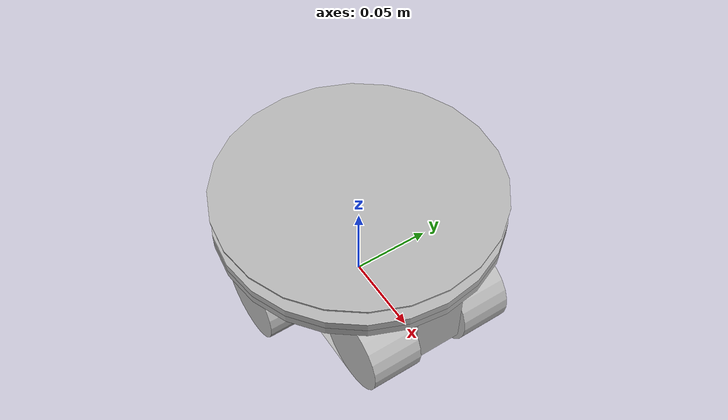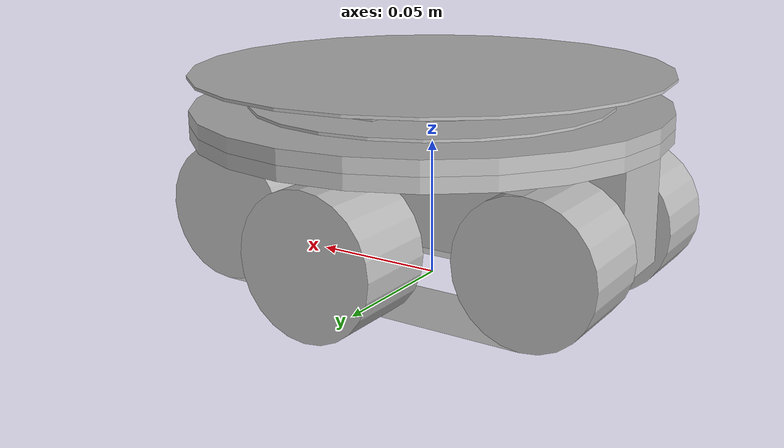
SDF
<?xml version='1.0'?>
<sdf version='1.6'>
		<model name="Marxbot">
			<self_collide>true</self_collide>
			<pose>0.0 0.0 0.0 0.0 0.0 0.0</pose>
			<!-- Start of parts of the pmodel Marxbot -->
				<!-- Start of declarations for part "Marxbot::p1" -->
					<!-- Start of parts of part "Marxbot::p1" -->
					<!-- Start of declarations for part "Marxbot::p1::LTreel" -->
						<!-- Start of parts of part "Marxbot::p1::LTreel" -->
						<!-- End of parts of part "Marxbot::p1::LTreel" -->

						<!-- Start of links of part "Marxbot::p1::LTreel" -->
						<!-- link full name is Marxbot::p1::LTreel::Wheel -->
						<link name="1-Wheel">
								<pose>0.0 0.059999998530114576 0.024997220650460422 -1.5709353129016326 -0.0 0.0</pose>
								<inertial>
									<pose>0.0 0.0 0.0 0.0 0.0 0.0</pose>
									<inertia>
										<ixx>1.0</ixx>
										<ixy>0.0</ixy>
										<ixz>0.0</ixz>
										<iyy>1.0</iyy>
										<iyz>0.0</iyz>
										<izz>1.0</izz>
									</inertia>
									<mass>1.0</mass>
								</inertial>
								<!-- body full name is Marxbot::p1::LTreel::Wheel::Wheel -->
								<collision name="1--Wheel">
									<laser_retro>0.0</laser_retro>
									<pose>0.0 0.0 0.0 0.0 0.0 0.0</pose>
									<geometry>
										<cylinder>
											<radius>0.025025001541152614</radius>
											<length>0.029999999329447746</length>
										</cylinder>
									</geometry>
									<surface>
										<bounce>
											<restitution_coefficient>0.0</restitution_coefficient>
											<threshold>100000.0</threshold>
										</bounce>
										<friction>
											<ode>
												<mu>1.0</mu>
												<mu2>1.0</mu2>
												<fdir1>0.0 0.0 0.0</fdir1>
												<slip1>0.0</slip1>
												<slip2>0.0</slip2>
											</ode>
											<torsional>
												<coefficient>1.0</coefficient>
												<surface_radius>0.0</surface_radius>
											</torsional>
										</friction>
									</surface>
								</collision>
								<visual name="1--Wheel">
									<laser_retro>0.0</laser_retro>
									<pose>0.0 0.0 0.0 0.0 0.0 0.0</pose>
									<geometry>
										<cylinder>
											<radius>0.025025001541152614</radius>
											<length>0.029999999329447746</length>
										</cylinder>
									</geometry>
									<surface>
										<bounce>
											<restitution_coefficient>0.0</restitution_coefficient>
											<threshold>100000.0</threshold>
										</bounce>
										<friction>
											<ode>
												<mu>1.0</mu>
												<mu2>1.0</mu2>
												<fdir1>0.0 0.0 0.0</fdir1>
												<slip1>0.0</slip1>
												<slip2>0.0</slip2>
											</ode>
											<torsional>
												<coefficient>1.0</coefficient>
												<surface_radius>0.0</surface_radius>
											</torsional>
										</friction>
									</surface>
								</visual>
						</link>
						<!-- link full name is Marxbot::p1::LTreel::Track -->
						<link name="2-Track">
								<pose>0.0 0.029999999329447746 0.02500000037252903 3.1414999961853027 0.0 0.0</pose>
								<inertial>
									<pose>0.0 0.0 0.0 0.0 0.0 0.0</pose>
									<inertia>
										<ixx>1.0</ixx>
										<ixy>0.0</ixy>
										<ixz>0.0</ixz>
										<iyy>1.0</iyy>
										<iyz>0.0</iyz>
										<izz>1.0</izz>
									</inertia>
									<mass>1.0</mass>
								</inertial>
								<!-- body full name is Marxbot::p1::LTreel::Track::Top -->
								<collision name="2--Top">
									<laser_retro>0.0</laser_retro>
									<pose>0.0 0.0 0.02500000037252903 0.0 0.0 0.0</pose>
									<geometry>
										<box>
											<size>0.12000000104308128 0.029999999329447746 0</size>
										</box>
									</geometry>
									<surface>
										<bounce>
											<restitution_coefficient>0.0</restitution_coefficient>
											<threshold>100000.0</threshold>
										</bounce>
										<friction>
											<ode>
												<mu>1.0</mu>
												<mu2>1.0</mu2>
												<fdir1>0.0 0.0 0.0</fdir1>
												<slip1>0.0</slip1>
												<slip2>0.0</slip2>
											</ode>
											<torsional>
												<coefficient>1.0</coefficient>
												<surface_radius>0.0</surface_radius>
											</torsional>
										</friction>
									</surface>
								</collision>
								<visual name="2--Top">
									<laser_retro>0.0</laser_retro>
									<pose>0.0 0.0 0.02500000037252903 0.0 0.0 0.0</pose>
									<geometry>
										<box>
											<size>0.12000000104308128 0.029999999329447746 0</size>
										</box>
									</geometry>
									<surface>
										<bounce>
											<restitution_coefficient>0.0</restitution_coefficient>
											<threshold>100000.0</threshold>
										</bounce>
										<friction>
											<ode>
												<mu>1.0</mu>
												<mu2>1.0</mu2>
												<fdir1>0.0 0.0 0.0</fdir1>
												<slip1>0.0</slip1>
												<slip2>0.0</slip2>
											</ode>
											<torsional>
												<coefficient>1.0</coefficient>
												<surface_radius>0.0</surface_radius>
											</torsional>
										</friction>
									</surface>
								</visual>
								<!-- body full name is Marxbot::p1::LTreel::Track::Bottom -->
								<collision name="3--Bottom">
									<laser_retro>0.0</laser_retro>
									<pose>0.0 0.0 -0.02500000037252903 0.0 0.0 0.0</pose>
									<geometry>
										<box>
											<size>0.12000000104308128 0.029999999329447746 0</size>
										</box>
									</geometry>
									<surface>
										<bounce>
											<restitution_coefficient>0.0</restitution_coefficient>
											<threshold>100000.0</threshold>
										</bounce>
										<friction>
											<ode>
												<mu>1.0</mu>
												<mu2>1.0</mu2>
												<fdir1>0.0 0.0 0.0</fdir1>
												<slip1>0.0</slip1>
												<slip2>0.0</slip2>
											</ode>
											<torsional>
												<coefficient>1.0</coefficient>
												<surface_radius>0.0</surface_radius>
											</torsional>
										</friction>
									</surface>
								</collision>
								<visual name="3--Bottom">
									<laser_retro>0.0</laser_retro>
									<pose>0.0 0.0 -0.02500000037252903 0.0 0.0 0.0</pose>
									<geometry>
										<box>
											<size>0.12000000104308128 0.029999999329447746 0</size>
										</box>
									</geometry>
									<surface>
										<bounce>
											<restitution_coefficient>0.0</restitution_coefficient>
											<threshold>100000.0</threshold>
										</bounce>
										<friction>
											<ode>
												<mu>1.0</mu>
												<mu2>1.0</mu2>
												<fdir1>0.0 0.0 0.0</fdir1>
												<slip1>0.0</slip1>
												<slip2>0.0</slip2>
											</ode>
											<torsional>
												<coefficient>1.0</coefficient>
												<surface_radius>0.0</surface_radius>
											</torsional>
										</friction>
									</surface>
								</visual>
								<!-- body full name is Marxbot::p1::LTreel::Track::FrontWheel -->
								<collision name="4--FrontWheel">
									<laser_retro>0.0</laser_retro>
									<pose>-0.06000000052154064 0.0 0.0 1.5707499980926514 0.0 0.0</pose>
									<geometry>
										<cylinder>
											<radius>0.02500000037252903</radius>
											<length>0.029999999329447746</length>
										</cylinder>
									</geometry>
									<surface>
										<bounce>
											<restitution_coefficient>0.0</restitution_coefficient>
											<threshold>100000.0</threshold>
										</bounce>
										<friction>
											<ode>
												<mu>1.0</mu>
												<mu2>1.0</mu2>
												<fdir1>0.0 0.0 0.0</fdir1>
												<slip1>0.0</slip1>
												<slip2>0.0</slip2>
											</ode>
											<torsional>
												<coefficient>1.0</coefficient>
												<surface_radius>0.0</surface_radius>
											</torsional>
										</friction>
									</surface>
								</collision>
								<visual name="4--FrontWheel">
									<laser_retro>0.0</laser_retro>
									<pose>-0.06000000052154064 0.0 0.0 1.5707499980926514 0.0 0.0</pose>
									<geometry>
										<cylinder>
											<radius>0.02500000037252903</radius>
											<length>0.029999999329447746</length>
										</cylinder>
									</geometry>
									<surface>
										<bounce>
											<restitution_coefficient>0.0</restitution_coefficient>
											<threshold>100000.0</threshold>
										</bounce>
										<friction>
											<ode>
												<mu>1.0</mu>
												<mu2>1.0</mu2>
												<fdir1>0.0 0.0 0.0</fdir1>
												<slip1>0.0</slip1>
												<slip2>0.0</slip2>
											</ode>
											<torsional>
												<coefficient>1.0</coefficient>
												<surface_radius>0.0</surface_radius>
											</torsional>
										</friction>
									</surface>
								</visual>
								<!-- body full name is Marxbot::p1::LTreel::Track::BackWheel -->
								<collision name="5--BackWheel">
									<laser_retro>0.0</laser_retro>
									<pose>0.06000000052154064 0.0 0.0 1.5707499980926514 0.0 0.0</pose>
									<geometry>
										<cylinder>
											<radius>0.02500000037252903</radius>
											<length>0.029999999329447746</length>
										</cylinder>
									</geometry>
									<surface>
										<bounce>
											<restitution_coefficient>0.0</restitution_coefficient>
											<threshold>100000.0</threshold>
										</bounce>
										<friction>
											<ode>
												<mu>1.0</mu>
												<mu2>1.0</mu2>
												<fdir1>0.0 0.0 0.0</fdir1>
												<slip1>0.0</slip1>
												<slip2>0.0</slip2>
											</ode>
											<torsional>
												<coefficient>1.0</coefficient>
												<surface_radius>0.0</surface_radius>
											</torsional>
										</friction>
									</surface>
								</collision>
								<visual name="5--BackWheel">
									<laser_retro>0.0</laser_retro>
									<pose>0.06000000052154064 0.0 0.0 1.5707499980926514 0.0 0.0</pose>
									<geometry>
										<cylinder>
											<radius>0.02500000037252903</radius>
											<length>0.029999999329447746</length>
										</cylinder>
									</geometry>
									<surface>
										<bounce>
											<restitution_coefficient>0.0</restitution_coefficient>
											<threshold>100000.0</threshold>
										</bounce>
										<friction>
											<ode>
												<mu>1.0</mu>
												<mu2>1.0</mu2>
												<fdir1>0.0 0.0 0.0</fdir1>
												<slip1>0.0</slip1>
												<slip2>0.0</slip2>
											</ode>
											<torsional>
												<coefficient>1.0</coefficient>
												<surface_radius>0.0</surface_radius>
											</torsional>
										</friction>
									</surface>
								</visual>
						</link>
						<!-- End of links of part "Marxbot::p1::LTreel" -->

						<!-- Start of joints of part "Marxbot::p1::LTreel" -->
						<!-- End of joints of part "Marxbot::p1::LTreel" -->

						<!-- Start of fixed connections of part "Marxbot::p1::LTreel" -->

						<!-- End of fixed connections of part "Marxbot::p1::LTreel" -->
					<!-- End of declarations for part "Marxbot::p1::LTreel" -->
					<!-- Start of declarations for part "Marxbot::p1::RTreel" -->
						<!-- Start of parts of part "Marxbot::p1::RTreel" -->
						<!-- End of parts of part "Marxbot::p1::RTreel" -->

						<!-- Start of links of part "Marxbot::p1::RTreel" -->
						<!-- link full name is Marxbot::p1::RTreel::Wheel -->
						<link name="3-Wheel">
								<pose>0.0 -0.05999999865889549 0.02500000037252903 1.5707499980926514 -0.0 0.0</pose>
								<inertial>
									<pose>0.0 0.0 0.0 0.0 0.0 0.0</pose>
									<inertia>
										<ixx>1.0</ixx>
										<ixy>0.0</ixy>
										<ixz>0.0</ixz>
										<iyy>1.0</iyy>
										<iyz>0.0</iyz>
										<izz>1.0</izz>
									</inertia>
									<mass>1.0</mass>
								</inertial>
								<!-- body full name is Marxbot::p1::RTreel::Wheel::Wheel -->
								<collision name="6--Wheel">
									<laser_retro>0.0</laser_retro>
									<pose>0.0 0.0 0.0 0.0 0.0 0.0</pose>
									<geometry>
										<cylinder>
											<radius>0.025025001541152614</radius>
											<length>0.029999999329447746</length>
										</cylinder>
									</geometry>
									<surface>
										<bounce>
											<restitution_coefficient>0.0</restitution_coefficient>
											<threshold>100000.0</threshold>
										</bounce>
										<friction>
											<ode>
												<mu>1.0</mu>
												<mu2>1.0</mu2>
												<fdir1>0.0 0.0 0.0</fdir1>
												<slip1>0.0</slip1>
												<slip2>0.0</slip2>
											</ode>
											<torsional>
												<coefficient>1.0</coefficient>
												<surface_radius>0.0</surface_radius>
											</torsional>
										</friction>
									</surface>
								</collision>
								<visual name="6--Wheel">
									<laser_retro>0.0</laser_retro>
									<pose>0.0 0.0 0.0 0.0 0.0 0.0</pose>
									<geometry>
										<cylinder>
											<radius>0.025025001541152614</radius>
											<length>0.029999999329447746</length>
										</cylinder>
									</geometry>
									<surface>
										<bounce>
											<restitution_coefficient>0.0</restitution_coefficient>
											<threshold>100000.0</threshold>
										</bounce>
										<friction>
											<ode>
												<mu>1.0</mu>
												<mu2>1.0</mu2>
												<fdir1>0.0 0.0 0.0</fdir1>
												<slip1>0.0</slip1>
												<slip2>0.0</slip2>
											</ode>
											<torsional>
												<coefficient>1.0</coefficient>
												<surface_radius>0.0</surface_radius>
											</torsional>
										</friction>
									</surface>
								</visual>
						</link>
						<!-- link full name is Marxbot::p1::RTreel::Track -->
						<link name="4-Track">
								<pose>0.0 -0.029999999329447746 0.02500000037252903 0.0 0.0 0.0</pose>
								<inertial>
									<pose>0.0 0.0 0.0 0.0 0.0 0.0</pose>
									<inertia>
										<ixx>1.0</ixx>
										<ixy>0.0</ixy>
										<ixz>0.0</ixz>
										<iyy>1.0</iyy>
										<iyz>0.0</iyz>
										<izz>1.0</izz>
									</inertia>
									<mass>1.0</mass>
								</inertial>
								<!-- body full name is Marxbot::p1::RTreel::Track::Top -->
								<collision name="7--Top">
									<laser_retro>0.0</laser_retro>
									<pose>0.0 0.0 0.02500000037252903 0.0 0.0 0.0</pose>
									<geometry>
										<box>
											<size>0.12000000104308128 0.029999999329447746 0</size>
										</box>
									</geometry>
									<surface>
										<bounce>
											<restitution_coefficient>0.0</restitution_coefficient>
											<threshold>100000.0</threshold>
										</bounce>
										<friction>
											<ode>
												<mu>1.0</mu>
												<mu2>1.0</mu2>
												<fdir1>0.0 0.0 0.0</fdir1>
												<slip1>0.0</slip1>
												<slip2>0.0</slip2>
											</ode>
											<torsional>
												<coefficient>1.0</coefficient>
												<surface_radius>0.0</surface_radius>
											</torsional>
										</friction>
									</surface>
								</collision>
								<visual name="7--Top">
									<laser_retro>0.0</laser_retro>
									<pose>0.0 0.0 0.02500000037252903 0.0 0.0 0.0</pose>
									<geometry>
										<box>
											<size>0.12000000104308128 0.029999999329447746 0</size>
										</box>
									</geometry>
									<surface>
										<bounce>
											<restitution_coefficient>0.0</restitution_coefficient>
											<threshold>100000.0</threshold>
										</bounce>
										<friction>
											<ode>
												<mu>1.0</mu>
												<mu2>1.0</mu2>
												<fdir1>0.0 0.0 0.0</fdir1>
												<slip1>0.0</slip1>
												<slip2>0.0</slip2>
											</ode>
											<torsional>
												<coefficient>1.0</coefficient>
												<surface_radius>0.0</surface_radius>
											</torsional>
										</friction>
									</surface>
								</visual>
								<!-- body full name is Marxbot::p1::RTreel::Track::Bottom -->
								<collision name="8--Bottom">
									<laser_retro>0.0</laser_retro>
									<pose>0.0 0.0 -0.02500000037252903 0.0 0.0 0.0</pose>
									<geometry>
										<box>
											<size>0.12000000104308128 0.029999999329447746 0</size>
										</box>
									</geometry>
									<surface>
										<bounce>
											<restitution_coefficient>0.0</restitution_coefficient>
											<threshold>100000.0</threshold>
										</bounce>
										<friction>
											<ode>
												<mu>1.0</mu>
												<mu2>1.0</mu2>
												<fdir1>0.0 0.0 0.0</fdir1>
												<slip1>0.0</slip1>
												<slip2>0.0</slip2>
											</ode>
											<torsional>
												<coefficient>1.0</coefficient>
												<surface_radius>0.0</surface_radius>
											</torsional>
										</friction>
									</surface>
								</collision>
								<visual name="8--Bottom">
									<laser_retro>0.0</laser_retro>
									<pose>0.0 0.0 -0.02500000037252903 0.0 0.0 0.0</pose>
									<geometry>
										<box>
											<size>0.12000000104308128 0.029999999329447746 0</size>
										</box>
									</geometry>
									<surface>
										<bounce>
											<restitution_coefficient>0.0</restitution_coefficient>
											<threshold>100000.0</threshold>
										</bounce>
										<friction>
											<ode>
												<mu>1.0</mu>
												<mu2>1.0</mu2>
												<fdir1>0.0 0.0 0.0</fdir1>
												<slip1>0.0</slip1>
												<slip2>0.0</slip2>
											</ode>
											<torsional>
												<coefficient>1.0</coefficient>
												<surface_radius>0.0</surface_radius>
											</torsional>
										</friction>
									</surface>
								</visual>
								<!-- body full name is Marxbot::p1::RTreel::Track::FrontWheel -->
								<collision name="9--FrontWheel">
									<laser_retro>0.0</laser_retro>
									<pose>-0.06000000052154064 0.0 0.0 1.5707499980926514 0.0 0.0</pose>
									<geometry>
										<cylinder>
											<radius>0.02500000037252903</radius>
											<length>0.029999999329447746</length>
										</cylinder>
									</geometry>
									<surface>
										<bounce>
											<restitution_coefficient>0.0</restitution_coefficient>
											<threshold>100000.0</threshold>
										</bounce>
										<friction>
											<ode>
												<mu>1.0</mu>
												<mu2>1.0</mu2>
												<fdir1>0.0 0.0 0.0</fdir1>
												<slip1>0.0</slip1>
												<slip2>0.0</slip2>
											</ode>
											<torsional>
												<coefficient>1.0</coefficient>
												<surface_radius>0.0</surface_radius>
											</torsional>
										</friction>
									</surface>
								</collision>
								<visual name="9--FrontWheel">
									<laser_retro>0.0</laser_retro>
									<pose>-0.06000000052154064 0.0 0.0 1.5707499980926514 0.0 0.0</pose>
									<geometry>
										<cylinder>
											<radius>0.02500000037252903</radius>
											<length>0.029999999329447746</length>
										</cylinder>
									</geometry>
									<surface>
										<bounce>
											<restitution_coefficient>0.0</restitution_coefficient>
											<threshold>100000.0</threshold>
										</bounce>
										<friction>
											<ode>
												<mu>1.0</mu>
												<mu2>1.0</mu2>
												<fdir1>0.0 0.0 0.0</fdir1>
												<slip1>0.0</slip1>
												<slip2>0.0</slip2>
											</ode>
											<torsional>
												<coefficient>1.0</coefficient>
												<surface_radius>0.0</surface_radius>
											</torsional>
										</friction>
									</surface>
								</visual>
								<!-- body full name is Marxbot::p1::RTreel::Track::BackWheel -->
								<collision name="10--BackWheel">
									<laser_retro>0.0</laser_retro>
									<pose>0.06000000052154064 0.0 0.0 1.5707499980926514 0.0 0.0</pose>
									<geometry>
										<cylinder>
											<radius>0.02500000037252903</radius>
											<length>0.029999999329447746</length>
										</cylinder>
									</geometry>
									<surface>
										<bounce>
											<restitution_coefficient>0.0</restitution_coefficient>
											<threshold>100000.0</threshold>
										</bounce>
										<friction>
											<ode>
												<mu>1.0</mu>
												<mu2>1.0</mu2>
												<fdir1>0.0 0.0 0.0</fdir1>
												<slip1>0.0</slip1>
												<slip2>0.0</slip2>
											</ode>
											<torsional>
												<coefficient>1.0</coefficient>
												<surface_radius>0.0</surface_radius>
											</torsional>
										</friction>
									</surface>
								</collision>
								<visual name="10--BackWheel">
									<laser_retro>0.0</laser_retro>
									<pose>0.06000000052154064 0.0 0.0 1.5707499980926514 0.0 0.0</pose>
									<geometry>
										<cylinder>
											<radius>0.02500000037252903</radius>
											<length>0.029999999329447746</length>
										</cylinder>
									</geometry>
									<surface>
										<bounce>
											<restitution_coefficient>0.0</restitution_coefficient>
											<threshold>100000.0</threshold>
										</bounce>
										<friction>
											<ode>
												<mu>1.0</mu>
												<mu2>1.0</mu2>
												<fdir1>0.0 0.0 0.0</fdir1>
												<slip1>0.0</slip1>
												<slip2>0.0</slip2>
											</ode>
											<torsional>
												<coefficient>1.0</coefficient>
												<surface_radius>0.0</surface_radius>
											</torsional>
										</friction>
									</surface>
								</visual>
						</link>
						<!-- End of links of part "Marxbot::p1::RTreel" -->

						<!-- Start of joints of part "Marxbot::p1::RTreel" -->
						<!-- End of joints of part "Marxbot::p1::RTreel" -->

						<!-- Start of fixed connections of part "Marxbot::p1::RTreel" -->

						<!-- End of fixed connections of part "Marxbot::p1::RTreel" -->
					<!-- End of declarations for part "Marxbot::p1::RTreel" -->
					<!-- End of parts of part "Marxbot::p1" -->

					<!-- Start of links of part "Marxbot::p1" -->
					<!-- link full name is Marxbot::p1::Core -->
					<link name="5-Core">
							<pose>0.0 0.0 0.057500001043081284 0.0 0.0 0.0</pose>
							<inertial>
								<pose>0.0 0.0 0.0 0.0 0.0 0.0</pose>
								<inertia>
									<ixx>1.0</ixx>
									<ixy>0.0</ixy>
									<ixz>0.0</ixz>
									<iyy>1.0</iyy>
									<iyz>0.0</iyz>
									<izz>1.0</izz>
								</inertia>
								<mass>1.0</mass>
							</inertial>
							<!-- body full name is Marxbot::p1::Core::Spine -->
							<collision name="11--Spine">
								<laser_retro>0.0</laser_retro>
								<pose>0.0 0.0 -0.02250000089406967 0.0 0.0 1.5707499980926514</pose>
								<geometry>
									<box>
										<size>0.029999999329447746 0.1599999964237213 0.03999999910593033</size>
									</box>
								</geometry>
								<surface>
									<bounce>
										<restitution_coefficient>0.0</restitution_coefficient>
										<threshold>100000.0</threshold>
									</bounce>
									<friction>
										<ode>
											<mu>1.0</mu>
											<mu2>1.0</mu2>
											<fdir1>0.0 0.0 0.0</fdir1>
											<slip1>0.0</slip1>
											<slip2>0.0</slip2>
										</ode>
										<torsional>
											<coefficient>1.0</coefficient>
											<surface_radius>0.0</surface_radius>
										</torsional>
									</friction>
								</surface>
							</collision>
							<visual name="11--Spine">
								<laser_retro>0.0</laser_retro>
								<pose>0.0 0.0 -0.02250000089406967 0.0 0.0 1.5707499980926514</pose>
								<geometry>
									<box>
										<size>0.029999999329447746 0.1599999964237213 0.03999999910593033</size>
									</box>
								</geometry>
								<surface>
									<bounce>
										<restitution_coefficient>0.0</restitution_coefficient>
										<threshold>100000.0</threshold>
									</bounce>
									<friction>
										<ode>
											<mu>1.0</mu>
											<mu2>1.0</mu2>
											<fdir1>0.0 0.0 0.0</fdir1>
											<slip1>0.0</slip1>
											<slip2>0.0</slip2>
										</ode>
										<torsional>
											<coefficient>1.0</coefficient>
											<surface_radius>0.0</surface_radius>
										</torsional>
									</friction>
								</surface>
							</visual>
							<!-- body full name is Marxbot::p1::Core::Frame -->
							<collision name="12--Frame">
								<laser_retro>0.0</laser_retro>
								<pose>0.0 0.0 0.0 0.0 0.0 0.0</pose>
								<geometry>
									<cylinder>
										<radius>0.08500000089406967</radius>
										<length>0.004999999888241291</length>
									</cylinder>
								</geometry>
								<surface>
									<bounce>
										<restitution_coefficient>0.0</restitution_coefficient>
										<threshold>100000.0</threshold>
									</bounce>
									<friction>
										<ode>
											<mu>1.0</mu>
											<mu2>1.0</mu2>
											<fdir1>0.0 0.0 0.0</fdir1>
											<slip1>0.0</slip1>
											<slip2>0.0</slip2>
										</ode>
										<torsional>
											<coefficient>1.0</coefficient>
											<surface_radius>0.0</surface_radius>
										</torsional>
									</friction>
								</surface>
							</collision>
							<visual name="12--Frame">
								<laser_retro>0.0</laser_retro>
								<pose>0.0 0.0 0.0 0.0 0.0 0.0</pose>
								<geometry>
									<cylinder>
										<radius>0.08500000089406967</radius>
										<length>0.004999999888241291</length>
									</cylinder>
								</geometry>
								<surface>
									<bounce>
										<restitution_coefficient>0.0</restitution_coefficient>
										<threshold>100000.0</threshold>
									</bounce>
									<friction>
										<ode>
											<mu>1.0</mu>
											<mu2>1.0</mu2>
											<fdir1>0.0 0.0 0.0</fdir1>
											<slip1>0.0</slip1>
											<slip2>0.0</slip2>
										</ode>
										<torsional>
											<coefficient>1.0</coefficient>
											<surface_radius>0.0</surface_radius>
										</torsional>
									</friction>
								</surface>
							</visual>
							<!-- WARNING: The SDF generator relies on annotations to specify in SDF aspects of the sensor that are
								 accounted for in the equations. -->
							<!-- sensor simple name is GroundSensorSpine1 -->
							<sensor name="GroundSensorSpine1" type="ray">
								<pose>0.05999999865889549 0.0 -0.04259999841451645 0.0 1.5707499980926514 0.0</pose>
								<visualize>true</visualize>
								<always_on>true</always_on>
								<update_rate>1</update_rate>
								<ray>
									<scan>
										<horizontal>
											<samples>1</samples>
											<resolution>1.0</resolution>
										</horizontal>
										<vertical>
											<samples>1</samples>
											<resolution>1.0</resolution>
										</vertical>
									</scan>
									<range>
										<min>0.0</min>
										<max>0.10000000149011612</max>
									</range>
								</ray>
							</sensor>
							<!-- WARNING: The SDF generator relies on annotations to specify in SDF aspects of the sensor that are
								 accounted for in the equations. -->
							<!-- sensor simple name is GroundSensorSpine2 -->
							<sensor name="GroundSensorSpine2" type="ray">
								<pose>0.029999999329447746 0.0 -0.04259999841451645 0.0 1.5707499980926514 0.0</pose>
								<visualize>true</visualize>
								<always_on>true</always_on>
								<update_rate>1</update_rate>
								<ray>
									<scan>
										<horizontal>
											<samples>1</samples>
											<resolution>1.0</resolution>
										</horizontal>
										<vertical>
											<samples>1</samples>
											<resolution>1.0</resolution>
										</vertical>
									</scan>
									<range>
										<min>0.0</min>
										<max>0.10000000149011612</max>
									</range>
								</ray>
							</sensor>
							<!-- WARNING: The SDF generator relies on annotations to specify in SDF aspects of the sensor that are
								 accounted for in the equations. -->
							<!-- sensor simple name is GroundSensorSpine3 -->
							<sensor name="GroundSensorSpine3" type="ray">
								<pose>-0.029999999329447746 0.0 -0.04259999841451645 0.0 1.5707499980926514 0.0</pose>
								<visualize>true</visualize>
								<always_on>true</always_on>
								<update_rate>1</update_rate>
								<ray>
									<scan>
										<horizontal>
											<samples>1</samples>
											<resolution>1.0</resolution>
										</horizontal>
										<vertical>
											<samples>1</samples>
											<resolution>1.0</resolution>
										</vertical>
									</scan>
									<range>
										<min>0.0</min>
										<max>0.10000000149011612</max>
									</range>
								</ray>
							</sensor>
							<!-- WARNING: The SDF generator relies on annotations to specify in SDF aspects of the sensor that are
								 accounted for in the equations. -->
							<!-- sensor simple name is GroundSensorSpine4 -->
							<sensor name="GroundSensorSpine4" type="ray">
								<pose>-0.05999999865889549 0.0 -0.04259999841451645 0.0 1.5707499980926514 0.0</pose>
								<visualize>true</visualize>
								<always_on>true</always_on>
								<update_rate>1</update_rate>
								<ray>
									<scan>
										<horizontal>
											<samples>1</samples>
											<resolution>1.0</resolution>
										</horizontal>
										<vertical>
											<samples>1</samples>
											<resolution>1.0</resolution>
										</vertical>
									</scan>
									<range>
										<min>0.0</min>
										<max>0.10000000149011612</max>
									</range>
								</ray>
							</sensor>
							<!-- WARNING: The SDF generator relies on annotations to specify in SDF aspects of the sensor that are
								 accounted for in the equations. -->
							<!-- sensor simple name is GroundSensorFrame -->
							<sensor name="GroundSensorFrame::0" type="ray">
								<pose>0.08299999684095383 0.0 -0.0024999999441206455 0.0 1.5707499980926514 0.0</pose>
								<visualize>true</visualize>
								<always_on>true</always_on>
								<update_rate>1</update_rate>
								<ray>
									<scan>
										<horizontal>
											<samples>1</samples>
											<resolution>1.0</resolution>
										</horizontal>
										<vertical>
											<samples>1</samples>
											<resolution>1.0</resolution>
										</vertical>
									</scan>
									<range>
										<min>0.0</min>
										<max>0.10000000149011612</max>
									</range>
								</ray>
							</sensor>
							<!-- WARNING: The SDF generator relies on annotations to specify in SDF aspects of the sensor that are
								 accounted for in the equations. -->
							<!-- sensor simple name is GroundSensorFrame -->
							<sensor name="GroundSensorFrame::1" type="ray">
								<pose>0.05869122010149262 0.0586885010764161 -0.0024999999441206455 0.0 1.5707499980926514 0.7853749990463257</pose>
								<visualize>true</visualize>
								<always_on>true</always_on>
								<update_rate>1</update_rate>
								<ray>
									<scan>
										<horizontal>
											<samples>1</samples>
											<resolution>1.0</resolution>
										</horizontal>
										<vertical>
											<samples>1</samples>
											<resolution>1.0</resolution>
										</vertical>
									</scan>
									<range>
										<min>0.0</min>
										<max>0.10000000149011612</max>
									</range>
								</ray>
							</sensor>
							<!-- WARNING: The SDF generator relies on annotations to specify in SDF aspects of the sensor that are
								 accounted for in the equations. -->
							<!-- sensor simple name is GroundSensorFrame -->
							<sensor name="GroundSensorFrame::2" type="ray">
								<pose>3.845282138625857E-6 0.08299999675188036 -0.0024999999441206455 0.0 1.5707499980926514 1.5707499980926514</pose>
								<visualize>true</visualize>
								<always_on>true</always_on>
								<update_rate>1</update_rate>
								<ray>
									<scan>
										<horizontal>
											<samples>1</samples>
											<resolution>1.0</resolution>
										</horizontal>
										<vertical>
											<samples>1</samples>
											<resolution>1.0</resolution>
										</vertical>
									</scan>
									<range>
										<min>0.0</min>
										<max>0.10000000149011612</max>
									</range>
								</ray>
							</sensor>
							<!-- WARNING: The SDF generator relies on annotations to specify in SDF aspects of the sensor that are
								 accounted for in the equations. -->
							<!-- sensor simple name is GroundSensorFrame -->
							<sensor name="GroundSensorFrame::3" type="ray">
								<pose>-0.05868578192537358 0.058693939000597335 -0.0024999999441206455 0.0 1.5707499980926514 2.356124997138977</pose>
								<visualize>true</visualize>
								<always_on>true</always_on>
								<update_rate>1</update_rate>
								<ray>
									<scan>
										<horizontal>
											<samples>1</samples>
											<resolution>1.0</resolution>
										</horizontal>
										<vertical>
											<samples>1</samples>
											<resolution>1.0</resolution>
										</vertical>
									</scan>
									<range>
										<min>0.0</min>
										<max>0.10000000149011612</max>
									</range>
								</ray>
							</sensor>
							<!-- WARNING: The SDF generator relies on annotations to specify in SDF aspects of the sensor that are
								 accounted for in the equations. -->
							<!-- sensor simple name is GroundSensorFrame -->
							<sensor name="GroundSensorFrame::4" type="ray">
								<pose>-0.08299999648465996 7.690564268998398E-6 -0.0024999999441206455 0.0 1.5707499980926514 3.1414999961853027</pose>
								<visualize>true</visualize>
								<always_on>true</always_on>
								<update_rate>1</update_rate>
								<ray>
									<scan>
										<horizontal>
											<samples>1</samples>
											<resolution>1.0</resolution>
										</horizontal>
										<vertical>
											<samples>1</samples>
											<resolution>1.0</resolution>
										</vertical>
									</scan>
									<range>
										<min>0.0</min>
										<max>0.10000000149011612</max>
									</range>
								</ray>
							</sensor>
							<!-- WARNING: The SDF generator relies on annotations to specify in SDF aspects of the sensor that are
								 accounted for in the equations. -->
							<!-- sensor simple name is GroundSensorFrame -->
							<sensor name="GroundSensorFrame::5" type="ray">
								<pose>-0.05869665777372438 -0.05868306264837092 -0.0024999999441206455 0.0 1.5707499980926514 3.9268749952316284</pose>
								<visualize>true</visualize>
								<always_on>true</always_on>
								<update_rate>1</update_rate>
								<ray>
									<scan>
										<horizontal>
											<samples>1</samples>
											<resolution>1.0</resolution>
										</horizontal>
										<vertical>
											<samples>1</samples>
											<resolution>1.0</resolution>
										</vertical>
									</scan>
									<range>
										<min>0.0</min>
										<max>0.10000000149011612</max>
									</range>
								</ray>
							</sensor>
							<!-- WARNING: The SDF generator relies on annotations to specify in SDF aspects of the sensor that are
								 accounted for in the equations. -->
							<!-- sensor simple name is GroundSensorFrame -->
							<sensor name="GroundSensorFrame::6" type="ray">
								<pose>-1.1535846382864308E-5 -0.08299999603929263 -0.0024999999441206455 0.0 1.5707499980926514 4.712249994277954</pose>
								<visualize>true</visualize>
								<always_on>true</always_on>
								<update_rate>1</update_rate>
								<ray>
									<scan>
										<horizontal>
											<samples>1</samples>
											<resolution>1.0</resolution>
										</horizontal>
										<vertical>
											<samples>1</samples>
											<resolution>1.0</resolution>
										</vertical>
									</scan>
									<range>
										<min>0.0</min>
										<max>0.10000000149011612</max>
									</range>
								</ray>
							</sensor>
							<!-- WARNING: The SDF generator relies on annotations to specify in SDF aspects of the sensor that are
								 accounted for in the equations. -->
							<!-- sensor simple name is GroundSensorFrame -->
							<sensor name="GroundSensorFrame::7" type="ray">
								<pose>0.05868034324541395 -0.058699376420867935 -0.0024999999441206455 0.0 1.5707499980926514 5.49762499332428</pose>
								<visualize>true</visualize>
								<always_on>true</always_on>
								<update_rate>1</update_rate>
								<ray>
									<scan>
										<horizontal>
											<samples>1</samples>
											<resolution>1.0</resolution>
										</horizontal>
										<vertical>
											<samples>1</samples>
											<resolution>1.0</resolution>
										</vertical>
									</scan>
									<range>
										<min>0.0</min>
										<max>0.10000000149011612</max>
									</range>
								</ray>
							</sensor>
							<!-- WARNING: The SDF generator relies on annotations to specify in SDF aspects of the sensor that are
								 accounted for in the equations. -->
							<!-- sensor simple name is Proximity -->
							<sensor name="Proximity::0" type="ray">
								<pose>0.08500000089406967 0.0 0.0 0.0 0.0 0.0</pose>
								<visualize>true</visualize>
								<always_on>true</always_on>
								<update_rate>1</update_rate>
								<ray>
									<scan>
										<horizontal>
											<samples>1</samples>
											<resolution>1.0</resolution>
										</horizontal>
										<vertical>
											<samples>1</samples>
											<resolution>1.0</resolution>
										</vertical>
									</scan>
									<range>
										<min>0.0</min>
										<max>0.10000000149011612</max>
									</range>
								</ray>
							</sensor>
							<!-- WARNING: The SDF generator relies on annotations to specify in SDF aspects of the sensor that are
								 accounted for in the equations. -->
							<!-- sensor simple name is Proximity -->
							<sensor name="Proximity::1" type="ray">
								<pose>0.08210386596469511 0.021998985104845752 0.0 0.0 0.0 0.2617916663487752</pose>
								<visualize>true</visualize>
								<always_on>true</always_on>
								<update_rate>1</update_rate>
								<ray>
									<scan>
										<horizontal>
											<samples>1</samples>
											<resolution>1.0</resolution>
										</horizontal>
										<vertical>
											<samples>1</samples>
											<resolution>1.0</resolution>
										</vertical>
									</scan>
									<range>
										<min>0.0</min>
										<max>0.10000000149011612</max>
									</range>
								</ray>
							</sensor>
							<!-- WARNING: The SDF generator relies on annotations to specify in SDF aspects of the sensor that are
								 accounted for in the equations. -->
							<!-- sensor simple name is Proximity -->
							<sensor name="Proximity::2" type="ray">
								<pose>0.07361281641047539 0.04249886365668487 0.0 0.0 0.0 0.5235833326975504</pose>
								<visualize>true</visualize>
								<always_on>true</always_on>
								<update_rate>1</update_rate>
								<ray>
									<scan>
										<horizontal>
											<samples>1</samples>
											<resolution>1.0</resolution>
										</horizontal>
										<vertical>
											<samples>1</samples>
											<resolution>1.0</resolution>
										</vertical>
									</scan>
									<range>
										<min>0.0</min>
										<max>0.10000000149011612</max>
									</range>
								</ray>
							</sensor>
							<!-- WARNING: The SDF generator relies on annotations to specify in SDF aspects of the sensor that are
								 accounted for in the equations. -->
							<!-- sensor simple name is Proximity -->
							<sensor name="Proximity::3" type="ray">
								<pose>0.060105469288877895 0.06010268474498956 0.0 0.0 0.0 0.7853749990463257</pose>
								<visualize>true</visualize>
								<always_on>true</always_on>
								<update_rate>1</update_rate>
								<ray>
									<scan>
										<horizontal>
											<samples>1</samples>
											<resolution>1.0</resolution>
										</horizontal>
										<vertical>
											<samples>1</samples>
											<resolution>1.0</resolution>
										</vertical>
									</scan>
									<range>
										<min>0.0</min>
										<max>0.10000000149011612</max>
									</range>
								</ray>
							</sensor>
							<!-- WARNING: The SDF generator relies on annotations to specify in SDF aspects of the sensor that are
								 accounted for in the equations. -->
							<!-- sensor simple name is Proximity -->
							<sensor name="Proximity::4" type="ray">
								<pose>0.04250227399732789 0.07361084741427659 0.0 0.0 0.0 1.0471666653951008</pose>
								<visualize>true</visualize>
								<always_on>true</always_on>
								<update_rate>1</update_rate>
								<ray>
									<scan>
										<horizontal>
											<samples>1</samples>
											<resolution>1.0</resolution>
										</horizontal>
										<vertical>
											<samples>1</samples>
											<resolution>1.0</resolution>
										</vertical>
									</scan>
									<range>
										<min>0.0</min>
										<max>0.10000000149011612</max>
									</range>
								</ray>
							</sensor>
							<!-- WARNING: The SDF generator relies on annotations to specify in SDF aspects of the sensor that are
								 accounted for in the equations. -->
							<!-- sensor simple name is Proximity -->
							<sensor name="Proximity::5" type="ray">
								<pose>0.0220027888467951 0.08210284669215309 0.0 0.0 0.0 1.3089583317438762</pose>
								<visualize>true</visualize>
								<always_on>true</always_on>
								<update_rate>1</update_rate>
								<ray>
									<scan>
										<horizontal>
											<samples>1</samples>
											<resolution>1.0</resolution>
										</horizontal>
										<vertical>
											<samples>1</samples>
											<resolution>1.0</resolution>
										</vertical>
									</scan>
									<range>
										<min>0.0</min>
										<max>0.10000000149011612</max>
									</range>
								</ray>
							</sensor>
							<!-- WARNING: The SDF generator relies on annotations to specify in SDF aspects of the sensor that are
								 accounted for in the equations. -->
							<!-- sensor simple name is Proximity -->
							<sensor name="Proximity::6" type="ray">
								<pose>3.9379397308588126E-6 0.08500000080284985 0.0 0.0 0.0 1.5707499980926514</pose>
								<visualize>true</visualize>
								<always_on>true</always_on>
								<update_rate>1</update_rate>
								<ray>
									<scan>
										<horizontal>
											<samples>1</samples>
											<resolution>1.0</resolution>
										</horizontal>
										<vertical>
											<samples>1</samples>
											<resolution>1.0</resolution>
										</vertical>
									</scan>
									<range>
										<min>0.0</min>
										<max>0.10000000149011612</max>
									</range>
								</ray>
							</sensor>
							<!-- WARNING: The SDF generator relies on annotations to specify in SDF aspects of the sensor that are
								 accounted for in the equations. -->
							<!-- sensor simple name is Proximity -->
							<sensor name="Proximity::7" type="ray">
								<pose>-0.021995181315678895 0.08210488506101361 0.0 0.0 0.0 1.8325416644414265</pose>
								<visualize>true</visualize>
								<always_on>true</always_on>
								<update_rate>1</update_rate>
								<ray>
									<scan>
										<horizontal>
											<samples>1</samples>
											<resolution>1.0</resolution>
										</horizontal>
										<vertical>
											<samples>1</samples>
											<resolution>1.0</resolution>
										</vertical>
									</scan>
									<range>
										<min>0.0</min>
										<max>0.10000000149011612</max>
									</range>
								</ray>
							</sensor>
							<!-- WARNING: The SDF generator relies on annotations to specify in SDF aspects of the sensor that are
								 accounted for in the equations. -->
							<!-- sensor simple name is Proximity -->
							<sensor name="Proximity::8" type="ray">
								<pose>-0.04249545322482448 0.07361478524867542 0.0 0.0 0.0 2.0943333307902017</pose>
								<visualize>true</visualize>
								<always_on>true</always_on>
								<update_rate>1</update_rate>
								<ray>
									<scan>
										<horizontal>
											<samples>1</samples>
											<resolution>1.0</resolution>
										</horizontal>
										<vertical>
											<samples>1</samples>
											<resolution>1.0</resolution>
										</vertical>
									</scan>
									<range>
										<min>0.0</min>
										<max>0.10000000149011612</max>
									</range>
								</ray>
							</sensor>
							<!-- WARNING: The SDF generator relies on annotations to specify in SDF aspects of the sensor that are
								 accounted for in the equations. -->
							<!-- sensor simple name is Proximity -->
							<sensor name="Proximity::9" type="ray">
								<pose>-0.0600999000720999 0.06010825370375895 0.0 0.0 0.0 2.356124997138977</pose>
								<visualize>true</visualize>
								<always_on>true</always_on>
								<update_rate>1</update_rate>
								<ray>
									<scan>
										<horizontal>
											<samples>1</samples>
											<resolution>1.0</resolution>
										</horizontal>
										<vertical>
											<samples>1</samples>
											<resolution>1.0</resolution>
										</vertical>
									</scan>
									<range>
										<min>0.0</min>
										<max>0.10000000149011612</max>
									</range>
								</ray>
							</sensor>
							<!-- WARNING: The SDF generator relies on annotations to specify in SDF aspects of the sensor that are
								 accounted for in the equations. -->
							<!-- sensor simple name is Proximity -->
							<sensor name="Proximity::10" type="ray">
								<pose>-0.07360887826008326 0.04250568424674618 0.0 0.0 0.0 2.6179166634877524</pose>
								<visualize>true</visualize>
								<always_on>true</always_on>
								<update_rate>1</update_rate>
								<ray>
									<scan>
										<horizontal>
											<samples>1</samples>
											<resolution>1.0</resolution>
										</horizontal>
										<vertical>
											<samples>1</samples>
											<resolution>1.0</resolution>
										</vertical>
									</scan>
									<range>
										<min>0.0</min>
										<max>0.10000000149011612</max>
									</range>
								</ray>
							</sensor>
							<!-- WARNING: The SDF generator relies on annotations to specify in SDF aspects of the sensor that are
								 accounted for in the equations. -->
							<!-- sensor simple name is Proximity -->
							<sensor name="Proximity::11" type="ray">
								<pose>-0.08210182724338974 0.02200659254151882 0.0 0.0 0.0 2.8797083298365274</pose>
								<visualize>true</visualize>
								<always_on>true</always_on>
								<update_rate>1</update_rate>
								<ray>
									<scan>
										<horizontal>
											<samples>1</samples>
											<resolution>1.0</resolution>
										</horizontal>
										<vertical>
											<samples>1</samples>
											<resolution>1.0</resolution>
										</vertical>
									</scan>
									<range>
										<min>0.0</min>
										<max>0.10000000149011612</max>
									</range>
								</ray>
							</sensor>
							<!-- WARNING: The SDF generator relies on annotations to specify in SDF aspects of the sensor that are
								 accounted for in the equations. -->
							<!-- sensor simple name is Proximity -->
							<sensor name="Proximity::12" type="ray">
								<pose>-0.08500000052919039 7.875879453265434E-6 0.0 0.0 0.0 3.1414999961853027</pose>
								<visualize>true</visualize>
								<always_on>true</always_on>
								<update_rate>1</update_rate>
								<ray>
									<scan>
										<horizontal>
											<samples>1</samples>
											<resolution>1.0</resolution>
										</horizontal>
										<vertical>
											<samples>1</samples>
											<resolution>1.0</resolution>
										</vertical>
									</scan>
									<range>
										<min>0.0</min>
										<max>0.10000000149011612</max>
									</range>
								</ray>
							</sensor>
							<!-- WARNING: The SDF generator relies on annotations to specify in SDF aspects of the sensor that are
								 accounted for in the equations. -->
							<!-- sensor simple name is Proximity -->
							<sensor name="Proximity::13" type="ray">
								<pose>-0.08210590398110638 -0.02199137747930274 0.0 0.0 0.0 3.403291662534078</pose>
								<visualize>true</visualize>
								<always_on>true</always_on>
								<update_rate>1</update_rate>
								<ray>
									<scan>
										<horizontal>
											<samples>1</samples>
											<resolution>1.0</resolution>
										</horizontal>
										<vertical>
											<samples>1</samples>
											<resolution>1.0</resolution>
										</vertical>
									</scan>
									<range>
										<min>0.0</min>
										<max>0.10000000149011612</max>
									</range>
								</ray>
							</sensor>
							<!-- WARNING: The SDF generator relies on annotations to specify in SDF aspects of the sensor that are
								 accounted for in the equations. -->
							<!-- sensor simple name is Proximity -->
							<sensor name="Proximity::14" type="ray">
								<pose>-0.07361675392887244 -0.04249204270175404 0.0 0.0 0.0 3.665083328882853</pose>
								<visualize>true</visualize>
								<always_on>true</always_on>
								<update_rate>1</update_rate>
								<ray>
									<scan>
										<horizontal>
											<samples>1</samples>
											<resolution>1.0</resolution>
										</horizontal>
										<vertical>
											<samples>1</samples>
											<resolution>1.0</resolution>
										</vertical>
									</scan>
									<range>
										<min>0.0</min>
										<max>0.10000000149011612</max>
									</range>
								</ray>
							</sensor>
							<!-- WARNING: The SDF generator relies on annotations to specify in SDF aspects of the sensor that are
								 accounted for in the equations. -->
							<!-- sensor simple name is Proximity -->
							<sensor name="Proximity::15" type="ray">
								<pose>-0.06011103798962673 -0.060097115270214906 0.0 0.0 0.0 3.9268749952316284</pose>
								<visualize>true</visualize>
								<always_on>true</always_on>
								<update_rate>1</update_rate>
								<ray>
									<scan>
										<horizontal>
											<samples>1</samples>
											<resolution>1.0</resolution>
										</horizontal>
										<vertical>
											<samples>1</samples>
											<resolution>1.0</resolution>
										</vertical>
									</scan>
									<range>
										<min>0.0</min>
										<max>0.10000000149011612</max>
									</range>
								</ray>
							</sensor>
							<!-- WARNING: The SDF generator relies on annotations to specify in SDF aspects of the sensor that are
								 accounted for in the equations. -->
							<!-- sensor simple name is Proximity -->
							<sensor name="Proximity::16" type="ray">
								<pose>-0.0425090944049325 -0.07360690894789959 0.0 0.0 0.0 4.188666661580403</pose>
								<visualize>true</visualize>
								<always_on>true</always_on>
								<update_rate>1</update_rate>
								<ray>
									<scan>
										<horizontal>
											<samples>1</samples>
											<resolution>1.0</resolution>
										</horizontal>
										<vertical>
											<samples>1</samples>
											<resolution>1.0</resolution>
										</vertical>
									</scan>
									<range>
										<min>0.0</min>
										<max>0.10000000149011612</max>
									</range>
								</ray>
							</sensor>
							<!-- WARNING: The SDF generator relies on annotations to specify in SDF aspects of the sensor that are
								 accounted for in the equations. -->
							<!-- sensor simple name is Proximity -->
							<sensor name="Proximity::17" type="ray">
								<pose>-0.02201039618900866 -0.08210080761840725 0.0 0.0 0.0 4.450458327929179</pose>
								<visualize>true</visualize>
								<always_on>true</always_on>
								<update_rate>1</update_rate>
								<ray>
									<scan>
										<horizontal>
											<samples>1</samples>
											<resolution>1.0</resolution>
										</horizontal>
										<vertical>
											<samples>1</samples>
											<resolution>1.0</resolution>
										</vertical>
									</scan>
									<range>
										<min>0.0</min>
										<max>0.10000000149011612</max>
									</range>
								</ray>
							</sensor>
							<!-- WARNING: The SDF generator relies on annotations to specify in SDF aspects of the sensor that are
								 accounted for in the equations. -->
							<!-- sensor simple name is Proximity -->
							<sensor name="Proximity::18" type="ray">
								<pose>-1.1813819158767672E-5 -0.0850000000730913 0.0 0.0 0.0 4.712249994277954</pose>
								<visualize>true</visualize>
								<always_on>true</always_on>
								<update_rate>1</update_rate>
								<ray>
									<scan>
										<horizontal>
											<samples>1</samples>
											<resolution>1.0</resolution>
										</horizontal>
										<vertical>
											<samples>1</samples>
											<resolution>1.0</resolution>
										</vertical>
									</scan>
									<range>
										<min>0.0</min>
										<max>0.10000000149011612</max>
									</range>
								</ray>
							</sensor>
							<!-- WARNING: The SDF generator relies on annotations to specify in SDF aspects of the sensor that are
								 accounted for in the equations. -->
							<!-- sensor simple name is Proximity -->
							<sensor name="Proximity::19" type="ray">
								<pose>0.021987573595725365 -0.08210692272497129 0.0 0.0 0.0 4.974041660626729</pose>
								<visualize>true</visualize>
								<always_on>true</always_on>
								<update_rate>1</update_rate>
								<ray>
									<scan>
										<horizontal>
											<samples>1</samples>
											<resolution>1.0</resolution>
										</horizontal>
										<vertical>
											<samples>1</samples>
											<resolution>1.0</resolution>
										</vertical>
									</scan>
									<range>
										<min>0.0</min>
										<max>0.10000000149011612</max>
									</range>
								</ray>
							</sensor>
							<!-- WARNING: The SDF generator relies on annotations to specify in SDF aspects of the sensor that are
								 accounted for in the equations. -->
							<!-- sensor simple name is Proximity -->
							<sensor name="Proximity::20" type="ray">
								<pose>0.04248863208748089 -0.07361872245106224 0.0 0.0 0.0 5.235833326975505</pose>
								<visualize>true</visualize>
								<always_on>true</always_on>
								<update_rate>1</update_rate>
								<ray>
									<scan>
										<horizontal>
											<samples>1</samples>
											<resolution>1.0</resolution>
										</horizontal>
										<vertical>
											<samples>1</samples>
											<resolution>1.0</resolution>
										</vertical>
									</scan>
									<range>
										<min>0.0</min>
										<max>0.10000000149011612</max>
									</range>
								</ray>
							</sensor>
							<!-- WARNING: The SDF generator relies on annotations to specify in SDF aspects of the sensor that are
								 accounted for in the equations. -->
							<!-- sensor simple name is Proximity -->
							<sensor name="Proximity::21" type="ray">
								<pose>0.06009433033934054 -0.06011382214647526 0.0 0.0 0.0 5.49762499332428</pose>
								<visualize>true</visualize>
								<always_on>true</always_on>
								<update_rate>1</update_rate>
								<ray>
									<scan>
										<horizontal>
											<samples>1</samples>
											<resolution>1.0</resolution>
										</horizontal>
										<vertical>
											<samples>1</samples>
											<resolution>1.0</resolution>
										</vertical>
									</scan>
									<range>
										<min>0.0</min>
										<max>0.10000000149011612</max>
									</range>
								</ray>
							</sensor>
							<!-- WARNING: The SDF generator relies on annotations to specify in SDF aspects of the sensor that are
								 accounted for in the equations. -->
							<!-- sensor simple name is Proximity -->
							<sensor name="Proximity::22" type="ray">
								<pose>0.07360493947772985 -0.04251250447187945 0.0 0.0 0.0 5.759416659673055</pose>
								<visualize>true</visualize>
								<always_on>true</always_on>
								<update_rate>1</update_rate>
								<ray>
									<scan>
										<horizontal>
											<samples>1</samples>
											<resolution>1.0</resolution>
										</horizontal>
										<vertical>
											<samples>1</samples>
											<resolution>1.0</resolution>
										</vertical>
									</scan>
									<range>
										<min>0.0</min>
										<max>0.10000000149011612</max>
									</range>
								</ray>
							</sensor>
							<!-- WARNING: The SDF generator relies on annotations to specify in SDF aspects of the sensor that are
								 accounted for in the equations. -->
							<!-- sensor simple name is Proximity -->
							<sensor name="Proximity::23" type="ray">
								<pose>0.0820997878172078 -0.022014199789256554 0.0 0.0 0.0 6.0212083260218305</pose>
								<visualize>true</visualize>
								<always_on>true</always_on>
								<update_rate>1</update_rate>
								<ray>
									<scan>
										<horizontal>
											<samples>1</samples>
											<resolution>1.0</resolution>
										</horizontal>
										<vertical>
											<samples>1</samples>
											<resolution>1.0</resolution>
										</vertical>
									</scan>
									<range>
										<min>0.0</min>
										<max>0.10000000149011612</max>
									</range>
								</ray>
							</sensor>
					</link>
					<!-- End of links of part "Marxbot::p1" -->

					<!-- Start of joints of part "Marxbot::p1" -->
					<!-- Full name of joint: Marxbot::p1::Core::LHinge from Marxbot::p1::Core to Marxbot::p1::LTreel::Wheel-->
					<joint name="6-LHinge" type="revolute">
						<pose>0.0 1.3879983906672777E-6 -0.029999999297511393 1.5709353129016326 -0.0 0.0</pose>
						<parent>5-Core</parent>
						<child>1-Wheel</child>
						<!-- WARNING: The SDF generator relies on annotations to specify in SDF aspects of the joint that are
							 accounted for in the equations. -->
						<axis>
							<xyz>0 1 0</xyz>
						</axis>
						<!-- WARNING: Annotation not found in actuator. RoboSim actuators have no explicit counterparts in SDF,
							 so the generator must rely on annotations to produce something meaningful in SDF. -->
					</joint>
					<!-- Full name of joint: Marxbot::p1::Core::RHinge from Marxbot::p1::Core to Marxbot::p1::RTreel::Wheel-->
					<joint name="7-RHinge" type="revolute">
						<pose>0.0 1.391723680937984E-6 -0.02999999929716622 -1.5707499980926514 -0.0 0.0</pose>
						<parent>5-Core</parent>
						<child>3-Wheel</child>
						<!-- WARNING: The SDF generator relies on annotations to specify in SDF aspects of the joint that are
							 accounted for in the equations. -->
						<axis>
							<xyz>0 -1 0</xyz>
						</axis>
						<!-- WARNING: Annotation not found in actuator. RoboSim actuators have no explicit counterparts in SDF,
							 so the generator must rely on annotations to produce something meaningful in SDF. -->
					</joint>
					<!-- End of joints of part "Marxbot::p1" -->

					<!-- Start of fixed connections of part "Marxbot::p1" -->
					<!-- fixed joint full name is Marxbot::p1::Core::fixedJoint::Marxbot::p2::Core from Marxbot::p1::Core to Marxbot::p2::Core -->
					<joint name="9-fixedJoint" type="fixed">
						<parent>5-Core</parent>
						<child>8-Core</child>
						<axis><xyz>0 0 1</xyz></axis>
					</joint>

					<!-- fixed joint full name is Marxbot::p1::Core::fixedJoint::Marxbot::p1::LTreel::Track from Marxbot::p1::Core to Marxbot::p1::LTreel::Track -->
					<joint name="10-fixedJoint" type="fixed">
						<parent>5-Core</parent>
						<child>2-Track</child>
						<axis><xyz>0 0 1</xyz></axis>
					</joint>
					<!-- fixed joint full name is Marxbot::p1::Core::fixedJoint::Marxbot::p1::RTreel::Track from Marxbot::p1::Core to Marxbot::p1::RTreel::Track -->
					<joint name="11-fixedJoint" type="fixed">
						<parent>5-Core</parent>
						<child>4-Track</child>
						<axis><xyz>0 0 1</xyz></axis>
					</joint>
					<!-- End of fixed connections of part "Marxbot::p1" -->
				<!-- End of declarations for part "Marxbot::p1" -->
				<!-- Start of declarations for part "Marxbot::p2" -->
					<!-- Start of parts of part "Marxbot::p2" -->
					<!-- End of parts of part "Marxbot::p2" -->

					<!-- Start of links of part "Marxbot::p2" -->
					<!-- link full name is Marxbot::p2::Core -->
					<link name="8-Core">
							<pose>0.0 0.0 0.0625 0.0 -0.0 0.0</pose>
							<inertial>
								<pose>0.0 0.0 0.0 0.0 0.0 0.0</pose>
								<inertia>
									<ixx>1.0</ixx>
									<ixy>0.0</ixy>
									<ixz>0.0</ixz>
									<iyy>1.0</iyy>
									<iyz>0.0</iyz>
									<izz>1.0</izz>
								</inertia>
								<mass>0.009999999776482582</mass>
							</inertial>
							<!-- body full name is Marxbot::p2::Core::Frame -->
							<collision name="13--Frame">
								<laser_retro>0.0</laser_retro>
								<pose>0.0 0.0 0.0 0.0 0.0 0.0</pose>
								<geometry>
									<cylinder>
										<radius>0.08500000089406967</radius>
										<length>0.004999999888241291</length>
									</cylinder>
								</geometry>
								<surface>
									<bounce>
										<restitution_coefficient>0.0</restitution_coefficient>
										<threshold>100000.0</threshold>
									</bounce>
									<friction>
										<ode>
											<mu>1.0</mu>
											<mu2>1.0</mu2>
											<fdir1>0.0 0.0 0.0</fdir1>
											<slip1>0.0</slip1>
											<slip2>0.0</slip2>
										</ode>
										<torsional>
											<coefficient>1.0</coefficient>
											<surface_radius>0.0</surface_radius>
										</torsional>
									</friction>
								</surface>
							</collision>
							<visual name="13--Frame">
								<laser_retro>0.0</laser_retro>
								<pose>0.0 0.0 0.0 0.0 0.0 0.0</pose>
								<geometry>
									<cylinder>
										<radius>0.08500000089406967</radius>
										<length>0.004999999888241291</length>
									</cylinder>
								</geometry>
								<surface>
									<bounce>
										<restitution_coefficient>0.0</restitution_coefficient>
										<threshold>100000.0</threshold>
									</bounce>
									<friction>
										<ode>
											<mu>1.0</mu>
											<mu2>1.0</mu2>
											<fdir1>0.0 0.0 0.0</fdir1>
											<slip1>0.0</slip1>
											<slip2>0.0</slip2>
										</ode>
										<torsional>
											<coefficient>1.0</coefficient>
											<surface_radius>0.0</surface_radius>
										</torsional>
									</friction>
								</surface>
							</visual>
							<!-- WARNING: The SDF generator relies on annotations to specify in SDF aspects of the sensor that are
								 accounted for in the equations. -->
							<!-- sensor simple name is IRSensor -->
							<sensor name="IRSensor::0" type="ray">
								<pose>0.08500000089406967 0.0 0.0 0.0 0.0 0.0</pose>
								<visualize>true</visualize>
								<always_on>true</always_on>
								<update_rate>1</update_rate>
								<ray>
									<scan>
										<horizontal>
											<samples>1</samples>
											<resolution>1.0</resolution>
										</horizontal>
										<vertical>
											<samples>1</samples>
											<resolution>1.0</resolution>
										</vertical>
									</scan>
									<range>
										<min>0.0</min>
										<max>0.10000000149011612</max>
									</range>
								</ray>
							</sensor>
							<!-- WARNING: The SDF generator relies on annotations to specify in SDF aspects of the sensor that are
								 accounted for in the equations. -->
							<!-- sensor simple name is IRSensor -->
							<sensor name="IRSensor::1" type="ray">
								<pose>0.060105469288877895 0.06010268474498956 0.0 0.0 0.0 0.7853749990463257</pose>
								<visualize>true</visualize>
								<always_on>true</always_on>
								<update_rate>1</update_rate>
								<ray>
									<scan>
										<horizontal>
											<samples>1</samples>
											<resolution>1.0</resolution>
										</horizontal>
										<vertical>
											<samples>1</samples>
											<resolution>1.0</resolution>
										</vertical>
									</scan>
									<range>
										<min>0.0</min>
										<max>0.10000000149011612</max>
									</range>
								</ray>
							</sensor>
							<!-- WARNING: The SDF generator relies on annotations to specify in SDF aspects of the sensor that are
								 accounted for in the equations. -->
							<!-- sensor simple name is IRSensor -->
							<sensor name="IRSensor::2" type="ray">
								<pose>3.9379397308588126E-6 0.08500000080284985 0.0 0.0 0.0 1.5707499980926514</pose>
								<visualize>true</visualize>
								<always_on>true</always_on>
								<update_rate>1</update_rate>
								<ray>
									<scan>
										<horizontal>
											<samples>1</samples>
											<resolution>1.0</resolution>
										</horizontal>
										<vertical>
											<samples>1</samples>
											<resolution>1.0</resolution>
										</vertical>
									</scan>
									<range>
										<min>0.0</min>
										<max>0.10000000149011612</max>
									</range>
								</ray>
							</sensor>
							<!-- WARNING: The SDF generator relies on annotations to specify in SDF aspects of the sensor that are
								 accounted for in the equations. -->
							<!-- sensor simple name is IRSensor -->
							<sensor name="IRSensor::3" type="ray">
								<pose>-0.0600999000720999 0.06010825370375895 0.0 0.0 0.0 2.356124997138977</pose>
								<visualize>true</visualize>
								<always_on>true</always_on>
								<update_rate>1</update_rate>
								<ray>
									<scan>
										<horizontal>
											<samples>1</samples>
											<resolution>1.0</resolution>
										</horizontal>
										<vertical>
											<samples>1</samples>
											<resolution>1.0</resolution>
										</vertical>
									</scan>
									<range>
										<min>0.0</min>
										<max>0.10000000149011612</max>
									</range>
								</ray>
							</sensor>
							<!-- WARNING: The SDF generator relies on annotations to specify in SDF aspects of the sensor that are
								 accounted for in the equations. -->
							<!-- sensor simple name is IRSensor -->
							<sensor name="IRSensor::4" type="ray">
								<pose>-0.08500000052919039 7.875879453265434E-6 0.0 0.0 0.0 3.1414999961853027</pose>
								<visualize>true</visualize>
								<always_on>true</always_on>
								<update_rate>1</update_rate>
								<ray>
									<scan>
										<horizontal>
											<samples>1</samples>
											<resolution>1.0</resolution>
										</horizontal>
										<vertical>
											<samples>1</samples>
											<resolution>1.0</resolution>
										</vertical>
									</scan>
									<range>
										<min>0.0</min>
										<max>0.10000000149011612</max>
									</range>
								</ray>
							</sensor>
							<!-- WARNING: The SDF generator relies on annotations to specify in SDF aspects of the sensor that are
								 accounted for in the equations. -->
							<!-- sensor simple name is IRSensor -->
							<sensor name="IRSensor::5" type="ray">
								<pose>-0.06011103798962673 -0.060097115270214906 0.0 0.0 0.0 3.9268749952316284</pose>
								<visualize>true</visualize>
								<always_on>true</always_on>
								<update_rate>1</update_rate>
								<ray>
									<scan>
										<horizontal>
											<samples>1</samples>
											<resolution>1.0</resolution>
										</horizontal>
										<vertical>
											<samples>1</samples>
											<resolution>1.0</resolution>
										</vertical>
									</scan>
									<range>
										<min>0.0</min>
										<max>0.10000000149011612</max>
									</range>
								</ray>
							</sensor>
							<!-- WARNING: The SDF generator relies on annotations to specify in SDF aspects of the sensor that are
								 accounted for in the equations. -->
							<!-- sensor simple name is IRSensor -->
							<sensor name="IRSensor::6" type="ray">
								<pose>-1.1813819158767672E-5 -0.0850000000730913 0.0 0.0 0.0 4.712249994277954</pose>
								<visualize>true</visualize>
								<always_on>true</always_on>
								<update_rate>1</update_rate>
								<ray>
									<scan>
										<horizontal>
											<samples>1</samples>
											<resolution>1.0</resolution>
										</horizontal>
										<vertical>
											<samples>1</samples>
											<resolution>1.0</resolution>
										</vertical>
									</scan>
									<range>
										<min>0.0</min>
										<max>0.10000000149011612</max>
									</range>
								</ray>
							</sensor>
							<!-- WARNING: The SDF generator relies on annotations to specify in SDF aspects of the sensor that are
								 accounted for in the equations. -->
							<!-- sensor simple name is IRSensor -->
							<sensor name="IRSensor::7" type="ray">
								<pose>0.06009433033934054 -0.06011382214647526 0.0 0.0 0.0 5.49762499332428</pose>
								<visualize>true</visualize>
								<always_on>true</always_on>
								<update_rate>1</update_rate>
								<ray>
									<scan>
										<horizontal>
											<samples>1</samples>
											<resolution>1.0</resolution>
										</horizontal>
										<vertical>
											<samples>1</samples>
											<resolution>1.0</resolution>
										</vertical>
									</scan>
									<range>
										<min>0.0</min>
										<max>0.10000000149011612</max>
									</range>
								</ray>
							</sensor>
							<!-- WARNING: Annotation not found in actuator. RoboSim actuators have no explicit counterparts in SDF,
								 so the generator must rely on annotations to produce something meaningful in SDF. -->
							<!-- WARNING: Annotation not found in actuator. RoboSim actuators have no explicit counterparts in SDF,
								 so the generator must rely on annotations to produce something meaningful in SDF. -->
							<!-- WARNING: Annotation not found in actuator. RoboSim actuators have no explicit counterparts in SDF,
								 so the generator must rely on annotations to produce something meaningful in SDF. -->
							<!-- WARNING: Annotation not found in actuator. RoboSim actuators have no explicit counterparts in SDF,
								 so the generator must rely on annotations to produce something meaningful in SDF. -->
							<!-- WARNING: Annotation not found in actuator. RoboSim actuators have no explicit counterparts in SDF,
								 so the generator must rely on annotations to produce something meaningful in SDF. -->
							<!-- WARNING: Annotation not found in actuator. RoboSim actuators have no explicit counterparts in SDF,
								 so the generator must rely on annotations to produce something meaningful in SDF. -->
							<!-- WARNING: Annotation not found in actuator. RoboSim actuators have no explicit counterparts in SDF,
								 so the generator must rely on annotations to produce something meaningful in SDF. -->
							<!-- WARNING: Annotation not found in actuator. RoboSim actuators have no explicit counterparts in SDF,
								 so the generator must rely on annotations to produce something meaningful in SDF. -->
							<!-- WARNING: Annotation not found in actuator. RoboSim actuators have no explicit counterparts in SDF,
								 so the generator must rely on annotations to produce something meaningful in SDF. -->
							<!-- WARNING: Annotation not found in actuator. RoboSim actuators have no explicit counterparts in SDF,
								 so the generator must rely on annotations to produce something meaningful in SDF. -->
							<!-- WARNING: Annotation not found in actuator. RoboSim actuators have no explicit counterparts in SDF,
								 so the generator must rely on annotations to produce something meaningful in SDF. -->
							<!-- WARNING: Annotation not found in actuator. RoboSim actuators have no explicit counterparts in SDF,
								 so the generator must rely on annotations to produce something meaningful in SDF. -->
							<!-- WARNING: Annotation not found in actuator. RoboSim actuators have no explicit counterparts in SDF,
								 so the generator must rely on annotations to produce something meaningful in SDF. -->
							<!-- WARNING: Annotation not found in actuator. RoboSim actuators have no explicit counterparts in SDF,
								 so the generator must rely on annotations to produce something meaningful in SDF. -->
							<!-- WARNING: Annotation not found in actuator. RoboSim actuators have no explicit counterparts in SDF,
								 so the generator must rely on annotations to produce something meaningful in SDF. -->
							<!-- WARNING: Annotation not found in actuator. RoboSim actuators have no explicit counterparts in SDF,
								 so the generator must rely on annotations to produce something meaningful in SDF. -->
					</link>
					<!-- End of links of part "Marxbot::p2" -->

					<!-- Start of joints of part "Marxbot::p2" -->
					<!-- End of joints of part "Marxbot::p2" -->

					<!-- Start of fixed connections of part "Marxbot::p2" -->
					<!-- fixed joint full name is Marxbot::p2::Core::fixedJoint::Marxbot::p3::Base from Marxbot::p2::Core to Marxbot::p3::Base -->
					<joint name="13-fixedJoint" type="fixed">
						<parent>8-Core</parent>
						<child>12-Base</child>
						<axis><xyz>0 0 1</xyz></axis>
					</joint>

					<!-- End of fixed connections of part "Marxbot::p2" -->
				<!-- End of declarations for part "Marxbot::p2" -->
				<!-- Start of declarations for part "Marxbot::p3" -->
					<!-- Start of parts of part "Marxbot::p3" -->
					<!-- Start of declarations for part "Marxbot::p3::longrange::0" -->
						<!-- Start of parts of part "Marxbot::p3::longrange::0" -->
						<!-- End of parts of part "Marxbot::p3::longrange::0" -->

						<!-- Start of links of part "Marxbot::p3::longrange::0" -->
						<!-- link full name is Marxbot::p3::longrange::0::BBody -->
						<link name="14-BBody">
								<pose>0.04399999976158142 0.0 0.07099999859929085 0.0 -0.0 0.0</pose>
								<inertial>
									<pose>0.0 0.0 0.0 0.0 0.0 0.0</pose>
									<inertia>
										<ixx>1.0</ixx>
										<ixy>0.0</ixy>
										<ixz>0.0</ixz>
										<iyy>1.0</iyy>
										<iyz>0.0</iyz>
										<izz>1.0</izz>
									</inertia>
									<mass>0.0010000000474974513</mass>
								</inertial>
								<!-- body full name is Marxbot::p3::longrange::0::BBody::Box -->
								<collision name="14--Box">
									<laser_retro>0.0</laser_retro>
									<pose>0.0 0.0 0.0 0.0 0.0 0.0</pose>
									<geometry>
										<box>
											<size>0.00800000037997961 0.01600000075995922 0.00800000037997961</size>
										</box>
									</geometry>
									<surface>
										<bounce>
											<restitution_coefficient>0.0</restitution_coefficient>
											<threshold>100000.0</threshold>
										</bounce>
										<friction>
											<ode>
												<mu>1.0</mu>
												<mu2>1.0</mu2>
												<fdir1>0.0 0.0 0.0</fdir1>
												<slip1>0.0</slip1>
												<slip2>0.0</slip2>
											</ode>
											<torsional>
												<coefficient>1.0</coefficient>
												<surface_radius>0.0</surface_radius>
											</torsional>
										</friction>
									</surface>
								</collision>
								<visual name="14--Box">
									<laser_retro>0.0</laser_retro>
									<pose>0.0 0.0 0.0 0.0 0.0 0.0</pose>
									<geometry>
										<box>
											<size>0.00800000037997961 0.01600000075995922 0.00800000037997961</size>
										</box>
									</geometry>
									<surface>
										<bounce>
											<restitution_coefficient>0.0</restitution_coefficient>
											<threshold>100000.0</threshold>
										</bounce>
										<friction>
											<ode>
												<mu>1.0</mu>
												<mu2>1.0</mu2>
												<fdir1>0.0 0.0 0.0</fdir1>
												<slip1>0.0</slip1>
												<slip2>0.0</slip2>
											</ode>
											<torsional>
												<coefficient>1.0</coefficient>
												<surface_radius>0.0</surface_radius>
											</torsional>
										</friction>
									</surface>
								</visual>
								<!-- WARNING: The SDF generator relies on annotations to specify in SDF aspects of the sensor that are
									 accounted for in the equations. -->
								<!-- sensor simple name is IRSensor -->
								<sensor name="IRSensor" type="ray">
									<pose>0.004000000189989805 -0.004000000189989805 0.0 0.0 0.0 0.0</pose>
									<visualize>true</visualize>
									<always_on>true</always_on>
									<update_rate>1</update_rate>
									<ray>
										<scan>
											<horizontal>
												<samples>1</samples>
												<resolution>1.0</resolution>
											</horizontal>
											<vertical>
												<samples>1</samples>
												<resolution>1.0</resolution>
											</vertical>
										</scan>
										<range>
											<min>0.0</min>
											<max>0.10000000149011612</max>
										</range>
									</ray>
								</sensor>
								<!-- WARNING: Annotation not found in actuator. RoboSim actuators have no explicit counterparts in SDF,
									 so the generator must rely on annotations to produce something meaningful in SDF. -->
						</link>
						<!-- End of links of part "Marxbot::p3::longrange::0" -->

						<!-- Start of joints of part "Marxbot::p3::longrange::0" -->
						<!-- End of joints of part "Marxbot::p3::longrange::0" -->

						<!-- Start of fixed connections of part "Marxbot::p3::longrange::0" -->

						<!-- End of fixed connections of part "Marxbot::p3::longrange::0" -->
					<!-- End of declarations for part "Marxbot::p3::longrange::0" -->
					<!-- Start of declarations for part "Marxbot::p3::longrange::1" -->
						<!-- Start of parts of part "Marxbot::p3::longrange::1" -->
						<!-- End of parts of part "Marxbot::p3::longrange::1" -->

						<!-- Start of links of part "Marxbot::p3::longrange::1" -->
						<!-- link full name is Marxbot::p3::longrange::1::BBody -->
						<link name="15-BBody">
								<pose>2.0384628870162577E-6 0.04399999971436175 0.07099999859929085 0.0 -0.0 1.5707499980926514</pose>
								<inertial>
									<pose>0.0 0.0 0.0 0.0 0.0 0.0</pose>
									<inertia>
										<ixx>1.0</ixx>
										<ixy>0.0</ixy>
										<ixz>0.0</ixz>
										<iyy>1.0</iyy>
										<iyz>0.0</iyz>
										<izz>1.0</izz>
									</inertia>
									<mass>0.0010000000474974513</mass>
								</inertial>
								<!-- body full name is Marxbot::p3::longrange::1::BBody::Box -->
								<collision name="15--Box">
									<laser_retro>0.0</laser_retro>
									<pose>0.0 0.0 0.0 0.0 0.0 0.0</pose>
									<geometry>
										<box>
											<size>0.00800000037997961 0.01600000075995922 0.00800000037997961</size>
										</box>
									</geometry>
									<surface>
										<bounce>
											<restitution_coefficient>0.0</restitution_coefficient>
											<threshold>100000.0</threshold>
										</bounce>
										<friction>
											<ode>
												<mu>1.0</mu>
												<mu2>1.0</mu2>
												<fdir1>0.0 0.0 0.0</fdir1>
												<slip1>0.0</slip1>
												<slip2>0.0</slip2>
											</ode>
											<torsional>
												<coefficient>1.0</coefficient>
												<surface_radius>0.0</surface_radius>
											</torsional>
										</friction>
									</surface>
								</collision>
								<visual name="15--Box">
									<laser_retro>0.0</laser_retro>
									<pose>0.0 0.0 0.0 0.0 0.0 0.0</pose>
									<geometry>
										<box>
											<size>0.00800000037997961 0.01600000075995922 0.00800000037997961</size>
										</box>
									</geometry>
									<surface>
										<bounce>
											<restitution_coefficient>0.0</restitution_coefficient>
											<threshold>100000.0</threshold>
										</bounce>
										<friction>
											<ode>
												<mu>1.0</mu>
												<mu2>1.0</mu2>
												<fdir1>0.0 0.0 0.0</fdir1>
												<slip1>0.0</slip1>
												<slip2>0.0</slip2>
											</ode>
											<torsional>
												<coefficient>1.0</coefficient>
												<surface_radius>0.0</surface_radius>
											</torsional>
										</friction>
									</surface>
								</visual>
								<!-- WARNING: The SDF generator relies on annotations to specify in SDF aspects of the sensor that are
									 accounted for in the equations. -->
								<!-- sensor simple name is IRSensor -->
								<sensor name="IRSensor" type="ray">
									<pose>0.004000000189989805 -0.004000000189989805 0.0 0.0 0.0 0.0</pose>
									<visualize>true</visualize>
									<always_on>true</always_on>
									<update_rate>1</update_rate>
									<ray>
										<scan>
											<horizontal>
												<samples>1</samples>
												<resolution>1.0</resolution>
											</horizontal>
											<vertical>
												<samples>1</samples>
												<resolution>1.0</resolution>
											</vertical>
										</scan>
										<range>
											<min>0.0</min>
											<max>0.10000000149011612</max>
										</range>
									</ray>
								</sensor>
								<!-- WARNING: Annotation not found in actuator. RoboSim actuators have no explicit counterparts in SDF,
									 so the generator must rely on annotations to produce something meaningful in SDF. -->
						</link>
						<!-- End of links of part "Marxbot::p3::longrange::1" -->

						<!-- Start of joints of part "Marxbot::p3::longrange::1" -->
						<!-- End of joints of part "Marxbot::p3::longrange::1" -->

						<!-- Start of fixed connections of part "Marxbot::p3::longrange::1" -->

						<!-- End of fixed connections of part "Marxbot::p3::longrange::1" -->
					<!-- End of declarations for part "Marxbot::p3::longrange::1" -->
					<!-- Start of declarations for part "Marxbot::p3::longrange::2" -->
						<!-- Start of parts of part "Marxbot::p3::longrange::2" -->
						<!-- End of parts of part "Marxbot::p3::longrange::2" -->

						<!-- Start of links of part "Marxbot::p3::longrange::2" -->
						<!-- link full name is Marxbot::p3::longrange::2::BBody -->
						<link name="16-BBody">
								<pose>-0.04399999957270274 4.076925769657263E-6 0.07099999859929085 0.0 -0.0 3.1414999961853027</pose>
								<inertial>
									<pose>0.0 0.0 0.0 0.0 0.0 0.0</pose>
									<inertia>
										<ixx>1.0</ixx>
										<ixy>0.0</ixy>
										<ixz>0.0</ixz>
										<iyy>1.0</iyy>
										<iyz>0.0</iyz>
										<izz>1.0</izz>
									</inertia>
									<mass>0.0010000000474974513</mass>
								</inertial>
								<!-- body full name is Marxbot::p3::longrange::2::BBody::Box -->
								<collision name="16--Box">
									<laser_retro>0.0</laser_retro>
									<pose>0.0 0.0 0.0 0.0 0.0 0.0</pose>
									<geometry>
										<box>
											<size>0.00800000037997961 0.01600000075995922 0.00800000037997961</size>
										</box>
									</geometry>
									<surface>
										<bounce>
											<restitution_coefficient>0.0</restitution_coefficient>
											<threshold>100000.0</threshold>
										</bounce>
										<friction>
											<ode>
												<mu>1.0</mu>
												<mu2>1.0</mu2>
												<fdir1>0.0 0.0 0.0</fdir1>
												<slip1>0.0</slip1>
												<slip2>0.0</slip2>
											</ode>
											<torsional>
												<coefficient>1.0</coefficient>
												<surface_radius>0.0</surface_radius>
											</torsional>
										</friction>
									</surface>
								</collision>
								<visual name="16--Box">
									<laser_retro>0.0</laser_retro>
									<pose>0.0 0.0 0.0 0.0 0.0 0.0</pose>
									<geometry>
										<box>
											<size>0.00800000037997961 0.01600000075995922 0.00800000037997961</size>
										</box>
									</geometry>
									<surface>
										<bounce>
											<restitution_coefficient>0.0</restitution_coefficient>
											<threshold>100000.0</threshold>
										</bounce>
										<friction>
											<ode>
												<mu>1.0</mu>
												<mu2>1.0</mu2>
												<fdir1>0.0 0.0 0.0</fdir1>
												<slip1>0.0</slip1>
												<slip2>0.0</slip2>
											</ode>
											<torsional>
												<coefficient>1.0</coefficient>
												<surface_radius>0.0</surface_radius>
											</torsional>
										</friction>
									</surface>
								</visual>
								<!-- WARNING: The SDF generator relies on annotations to specify in SDF aspects of the sensor that are
									 accounted for in the equations. -->
								<!-- sensor simple name is IRSensor -->
								<sensor name="IRSensor" type="ray">
									<pose>0.004000000189989805 -0.004000000189989805 0.0 0.0 0.0 0.0</pose>
									<visualize>true</visualize>
									<always_on>true</always_on>
									<update_rate>1</update_rate>
									<ray>
										<scan>
											<horizontal>
												<samples>1</samples>
												<resolution>1.0</resolution>
											</horizontal>
											<vertical>
												<samples>1</samples>
												<resolution>1.0</resolution>
											</vertical>
										</scan>
										<range>
											<min>0.0</min>
											<max>0.10000000149011612</max>
										</range>
									</ray>
								</sensor>
								<!-- WARNING: Annotation not found in actuator. RoboSim actuators have no explicit counterparts in SDF,
									 so the generator must rely on annotations to produce something meaningful in SDF. -->
						</link>
						<!-- End of links of part "Marxbot::p3::longrange::2" -->

						<!-- Start of joints of part "Marxbot::p3::longrange::2" -->
						<!-- End of joints of part "Marxbot::p3::longrange::2" -->

						<!-- Start of fixed connections of part "Marxbot::p3::longrange::2" -->

						<!-- End of fixed connections of part "Marxbot::p3::longrange::2" -->
					<!-- End of declarations for part "Marxbot::p3::longrange::2" -->
					<!-- Start of declarations for part "Marxbot::p3::longrange::3" -->
						<!-- Start of parts of part "Marxbot::p3::longrange::3" -->
						<!-- End of parts of part "Marxbot::p3::longrange::3" -->

						<!-- Start of links of part "Marxbot::p3::longrange::3" -->
						<!-- link full name is Marxbot::p3::longrange::3::BBody -->
						<link name="17-BBody">
								<pose>-6.115388643547765E-6 -0.04399999933660439 0.07099999859929085 0.0 -0.0 -1.5709353129016326</pose>
								<inertial>
									<pose>0.0 0.0 0.0 0.0 0.0 0.0</pose>
									<inertia>
										<ixx>1.0</ixx>
										<ixy>0.0</ixy>
										<ixz>0.0</ixz>
										<iyy>1.0</iyy>
										<iyz>0.0</iyz>
										<izz>1.0</izz>
									</inertia>
									<mass>0.0010000000474974513</mass>
								</inertial>
								<!-- body full name is Marxbot::p3::longrange::3::BBody::Box -->
								<collision name="17--Box">
									<laser_retro>0.0</laser_retro>
									<pose>0.0 0.0 0.0 0.0 0.0 0.0</pose>
									<geometry>
										<box>
											<size>0.00800000037997961 0.01600000075995922 0.00800000037997961</size>
										</box>
									</geometry>
									<surface>
										<bounce>
											<restitution_coefficient>0.0</restitution_coefficient>
											<threshold>100000.0</threshold>
										</bounce>
										<friction>
											<ode>
												<mu>1.0</mu>
												<mu2>1.0</mu2>
												<fdir1>0.0 0.0 0.0</fdir1>
												<slip1>0.0</slip1>
												<slip2>0.0</slip2>
											</ode>
											<torsional>
												<coefficient>1.0</coefficient>
												<surface_radius>0.0</surface_radius>
											</torsional>
										</friction>
									</surface>
								</collision>
								<visual name="17--Box">
									<laser_retro>0.0</laser_retro>
									<pose>0.0 0.0 0.0 0.0 0.0 0.0</pose>
									<geometry>
										<box>
											<size>0.00800000037997961 0.01600000075995922 0.00800000037997961</size>
										</box>
									</geometry>
									<surface>
										<bounce>
											<restitution_coefficient>0.0</restitution_coefficient>
											<threshold>100000.0</threshold>
										</bounce>
										<friction>
											<ode>
												<mu>1.0</mu>
												<mu2>1.0</mu2>
												<fdir1>0.0 0.0 0.0</fdir1>
												<slip1>0.0</slip1>
												<slip2>0.0</slip2>
											</ode>
											<torsional>
												<coefficient>1.0</coefficient>
												<surface_radius>0.0</surface_radius>
											</torsional>
										</friction>
									</surface>
								</visual>
								<!-- WARNING: The SDF generator relies on annotations to specify in SDF aspects of the sensor that are
									 accounted for in the equations. -->
								<!-- sensor simple name is IRSensor -->
								<sensor name="IRSensor" type="ray">
									<pose>0.004000000189989805 -0.004000000189989805 0.0 0.0 0.0 0.0</pose>
									<visualize>true</visualize>
									<always_on>true</always_on>
									<update_rate>1</update_rate>
									<ray>
										<scan>
											<horizontal>
												<samples>1</samples>
												<resolution>1.0</resolution>
											</horizontal>
											<vertical>
												<samples>1</samples>
												<resolution>1.0</resolution>
											</vertical>
										</scan>
										<range>
											<min>0.0</min>
											<max>0.10000000149011612</max>
										</range>
									</ray>
								</sensor>
								<!-- WARNING: Annotation not found in actuator. RoboSim actuators have no explicit counterparts in SDF,
									 so the generator must rely on annotations to produce something meaningful in SDF. -->
						</link>
						<!-- End of links of part "Marxbot::p3::longrange::3" -->

						<!-- Start of joints of part "Marxbot::p3::longrange::3" -->
						<!-- End of joints of part "Marxbot::p3::longrange::3" -->

						<!-- Start of fixed connections of part "Marxbot::p3::longrange::3" -->

						<!-- End of fixed connections of part "Marxbot::p3::longrange::3" -->
					<!-- End of declarations for part "Marxbot::p3::longrange::3" -->
					<!-- End of parts of part "Marxbot::p3" -->

					<!-- Start of links of part "Marxbot::p3" -->
					<!-- link full name is Marxbot::p3::Base -->
					<link name="12-Base">
							<pose>0.0 0.0 0.06549999862909317 0.0 -0.0 0.0</pose>
							<inertial>
								<pose>0.0 0.0 0.0 0.0 0.0 0.0</pose>
								<inertia>
									<ixx>1.0</ixx>
									<ixy>0.0</ixy>
									<ixz>0.0</ixz>
									<iyy>1.0</iyy>
									<iyz>0.0</iyz>
									<izz>1.0</izz>
								</inertia>
								<mass>0.009999999776482582</mass>
							</inertial>
							<!-- body full name is Marxbot::p3::Base::Frame -->
							<collision name="18--Frame">
								<laser_retro>0.0</laser_retro>
								<pose>0.0 0.0 0.0 0.0 0.0 0.0</pose>
								<geometry>
									<cylinder>
										<radius>0.06499999761581421</radius>
										<length>0.0010000000474974513</length>
									</cylinder>
								</geometry>
								<surface>
									<bounce>
										<restitution_coefficient>0.0</restitution_coefficient>
										<threshold>100000.0</threshold>
									</bounce>
									<friction>
										<ode>
											<mu>1.0</mu>
											<mu2>1.0</mu2>
											<fdir1>0.0 0.0 0.0</fdir1>
											<slip1>0.0</slip1>
											<slip2>0.0</slip2>
										</ode>
										<torsional>
											<coefficient>1.0</coefficient>
											<surface_radius>0.0</surface_radius>
										</torsional>
									</friction>
								</surface>
							</collision>
							<visual name="18--Frame">
								<laser_retro>0.0</laser_retro>
								<pose>0.0 0.0 0.0 0.0 0.0 0.0</pose>
								<geometry>
									<cylinder>
										<radius>0.06499999761581421</radius>
										<length>0.0010000000474974513</length>
									</cylinder>
								</geometry>
								<surface>
									<bounce>
										<restitution_coefficient>0.0</restitution_coefficient>
										<threshold>100000.0</threshold>
									</bounce>
									<friction>
										<ode>
											<mu>1.0</mu>
											<mu2>1.0</mu2>
											<fdir1>0.0 0.0 0.0</fdir1>
											<slip1>0.0</slip1>
											<slip2>0.0</slip2>
										</ode>
										<torsional>
											<coefficient>1.0</coefficient>
											<surface_radius>0.0</surface_radius>
										</torsional>
									</friction>
								</surface>
							</visual>
					</link>
					<!-- link full name is Marxbot::p3::Core -->
					<link name="18-Core">
							<pose>0.0 0.0 0.07099999859929085 0.0 -0.0 0.0</pose>
							<inertial>
								<pose>0.0 0.0 0.0 0.0 0.0 0.0</pose>
								<inertia>
									<ixx>1.0</ixx>
									<ixy>0.0</ixy>
									<ixz>0.0</ixz>
									<iyy>1.0</iyy>
									<iyz>0.0</iyz>
									<izz>1.0</izz>
								</inertia>
								<mass>1.0</mass>
							</inertial>
							<!-- body full name is Marxbot::p3::Core::Spine -->
							<collision name="19--Spine">
								<laser_retro>0.0</laser_retro>
								<pose>0.0 0.0 0.0 0.0 0.0 0.0</pose>
								<geometry>
									<cylinder>
										<radius>0.03999999910593033</radius>
										<length>0.009999999776482582</length>
									</cylinder>
								</geometry>
								<surface>
									<bounce>
										<restitution_coefficient>0.0</restitution_coefficient>
										<threshold>100000.0</threshold>
									</bounce>
									<friction>
										<ode>
											<mu>1.0</mu>
											<mu2>1.0</mu2>
											<fdir1>0.0 0.0 0.0</fdir1>
											<slip1>0.0</slip1>
											<slip2>0.0</slip2>
										</ode>
										<torsional>
											<coefficient>1.0</coefficient>
											<surface_radius>0.0</surface_radius>
										</torsional>
									</friction>
								</surface>
							</collision>
							<visual name="19--Spine">
								<laser_retro>0.0</laser_retro>
								<pose>0.0 0.0 0.0 0.0 0.0 0.0</pose>
								<geometry>
									<cylinder>
										<radius>0.03999999910593033</radius>
										<length>0.009999999776482582</length>
									</cylinder>
								</geometry>
								<surface>
									<bounce>
										<restitution_coefficient>0.0</restitution_coefficient>
										<threshold>100000.0</threshold>
									</bounce>
									<friction>
										<ode>
											<mu>1.0</mu>
											<mu2>1.0</mu2>
											<fdir1>0.0 0.0 0.0</fdir1>
											<slip1>0.0</slip1>
											<slip2>0.0</slip2>
										</ode>
										<torsional>
											<coefficient>1.0</coefficient>
											<surface_radius>0.0</surface_radius>
										</torsional>
									</friction>
								</surface>
							</visual>
							<!-- body full name is Marxbot::p3::Core::Top -->
							<collision name="20--Top">
								<laser_retro>0.0</laser_retro>
								<pose>0.0 0.0 0.005499999970197678 0.0 0.0 0.0</pose>
								<geometry>
									<cylinder>
										<radius>0.08500000089406967</radius>
										<length>0.0010000000474974513</length>
									</cylinder>
								</geometry>
								<surface>
									<bounce>
										<restitution_coefficient>0.0</restitution_coefficient>
										<threshold>100000.0</threshold>
									</bounce>
									<friction>
										<ode>
											<mu>1.0</mu>
											<mu2>1.0</mu2>
											<fdir1>0.0 0.0 0.0</fdir1>
											<slip1>0.0</slip1>
											<slip2>0.0</slip2>
										</ode>
										<torsional>
											<coefficient>1.0</coefficient>
											<surface_radius>0.0</surface_radius>
										</torsional>
									</friction>
								</surface>
							</collision>
							<visual name="20--Top">
								<laser_retro>0.0</laser_retro>
								<pose>0.0 0.0 0.005499999970197678 0.0 0.0 0.0</pose>
								<geometry>
									<cylinder>
										<radius>0.08500000089406967</radius>
										<length>0.0010000000474974513</length>
									</cylinder>
								</geometry>
								<surface>
									<bounce>
										<restitution_coefficient>0.0</restitution_coefficient>
										<threshold>100000.0</threshold>
									</bounce>
									<friction>
										<ode>
											<mu>1.0</mu>
											<mu2>1.0</mu2>
											<fdir1>0.0 0.0 0.0</fdir1>
											<slip1>0.0</slip1>
											<slip2>0.0</slip2>
										</ode>
										<torsional>
											<coefficient>1.0</coefficient>
											<surface_radius>0.0</surface_radius>
										</torsional>
									</friction>
								</surface>
							</visual>
					</link>
					<!-- End of links of part "Marxbot::p3" -->

					<!-- Start of joints of part "Marxbot::p3" -->
					<!-- Full name of joint: Marxbot::p3::Base::rj from Marxbot::p3::Base to Marxbot::p3::Core-->
					<joint name="19-rj" type="revolute">
						<pose>0.0 0.0 -0.005499999970197678 0.0 -0.0 0.0</pose>
						<parent>12-Base</parent>
						<child>18-Core</child>
						<!-- WARNING: The SDF generator relies on annotations to specify in SDF aspects of the joint that are
							 accounted for in the equations. -->
						<axis>
							<xyz>0 0 1</xyz>
						</axis>
					</joint>
					<!-- End of joints of part "Marxbot::p3" -->

					<!-- Start of fixed connections of part "Marxbot::p3" -->

					<!-- fixed joint full name is Marxbot::p3::Core::fixedJoint::Marxbot::p3::longrange::2::BBody from Marxbot::p3::Core to Marxbot::p3::longrange::2::BBody -->
					<joint name="20-fixedJoint" type="fixed">
						<parent>18-Core</parent>
						<child>16-BBody</child>
						<axis><xyz>0 0 1</xyz></axis>
					</joint>
					<!-- fixed joint full name is Marxbot::p3::Core::fixedJoint::Marxbot::p3::longrange::3::BBody from Marxbot::p3::Core to Marxbot::p3::longrange::3::BBody -->
					<joint name="21-fixedJoint" type="fixed">
						<parent>18-Core</parent>
						<child>17-BBody</child>
						<axis><xyz>0 0 1</xyz></axis>
					</joint>
					<!-- fixed joint full name is Marxbot::p3::Core::fixedJoint::Marxbot::p3::longrange::0::BBody from Marxbot::p3::Core to Marxbot::p3::longrange::0::BBody -->
					<joint name="22-fixedJoint" type="fixed">
						<parent>18-Core</parent>
						<child>14-BBody</child>
						<axis><xyz>0 0 1</xyz></axis>
					</joint>
					<!-- fixed joint full name is Marxbot::p3::Core::fixedJoint::Marxbot::p3::longrange::1::BBody from Marxbot::p3::Core to Marxbot::p3::longrange::1::BBody -->
					<joint name="23-fixedJoint" type="fixed">
						<parent>18-Core</parent>
						<child>15-BBody</child>
						<axis><xyz>0 0 1</xyz></axis>
					</joint>
					<!-- End of fixed connections of part "Marxbot::p3" -->
				<!-- End of declarations for part "Marxbot::p3" -->
			<!-- End of parts of the pmodel Marxbot -->

			<!-- Start of links of the pmodel Marxbot -->
			<!-- End of links of the pmodel Marxbot -->

			<!-- Start of joints of the pmodel Marxbot -->
			<!-- End of joints of the pmodel Marxbot -->

			<!-- Start of fixed connections of the pmodel Marxbot -->
			<!-- End of fixed connections of the pmodel Marxbot -->
		</model>
</sdf>
